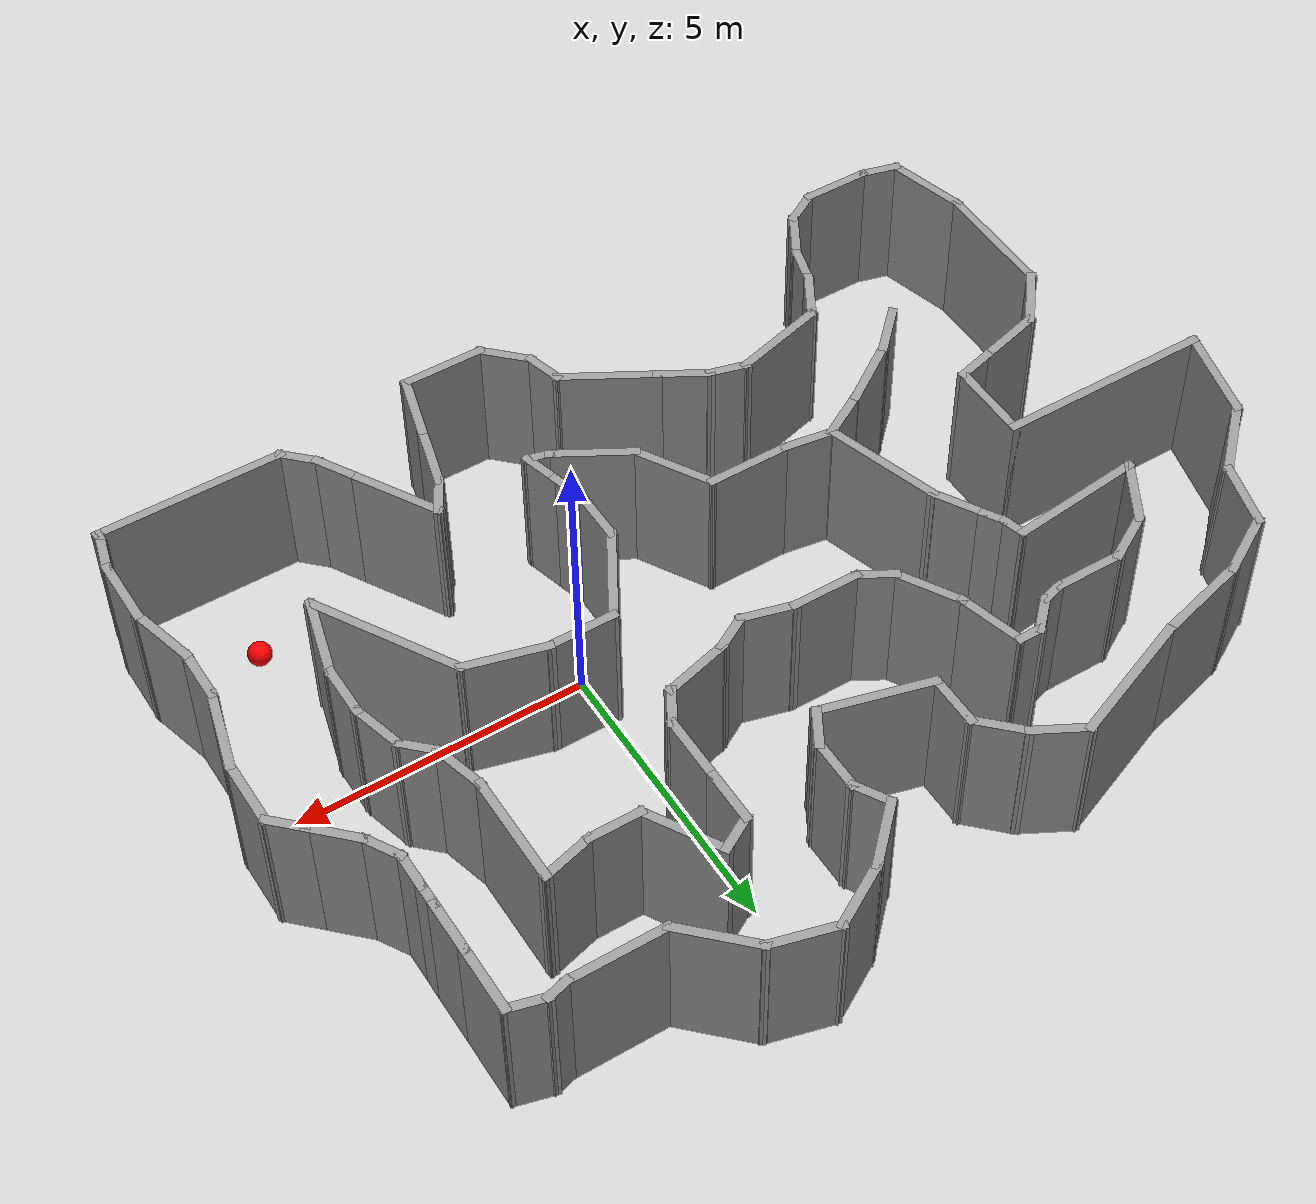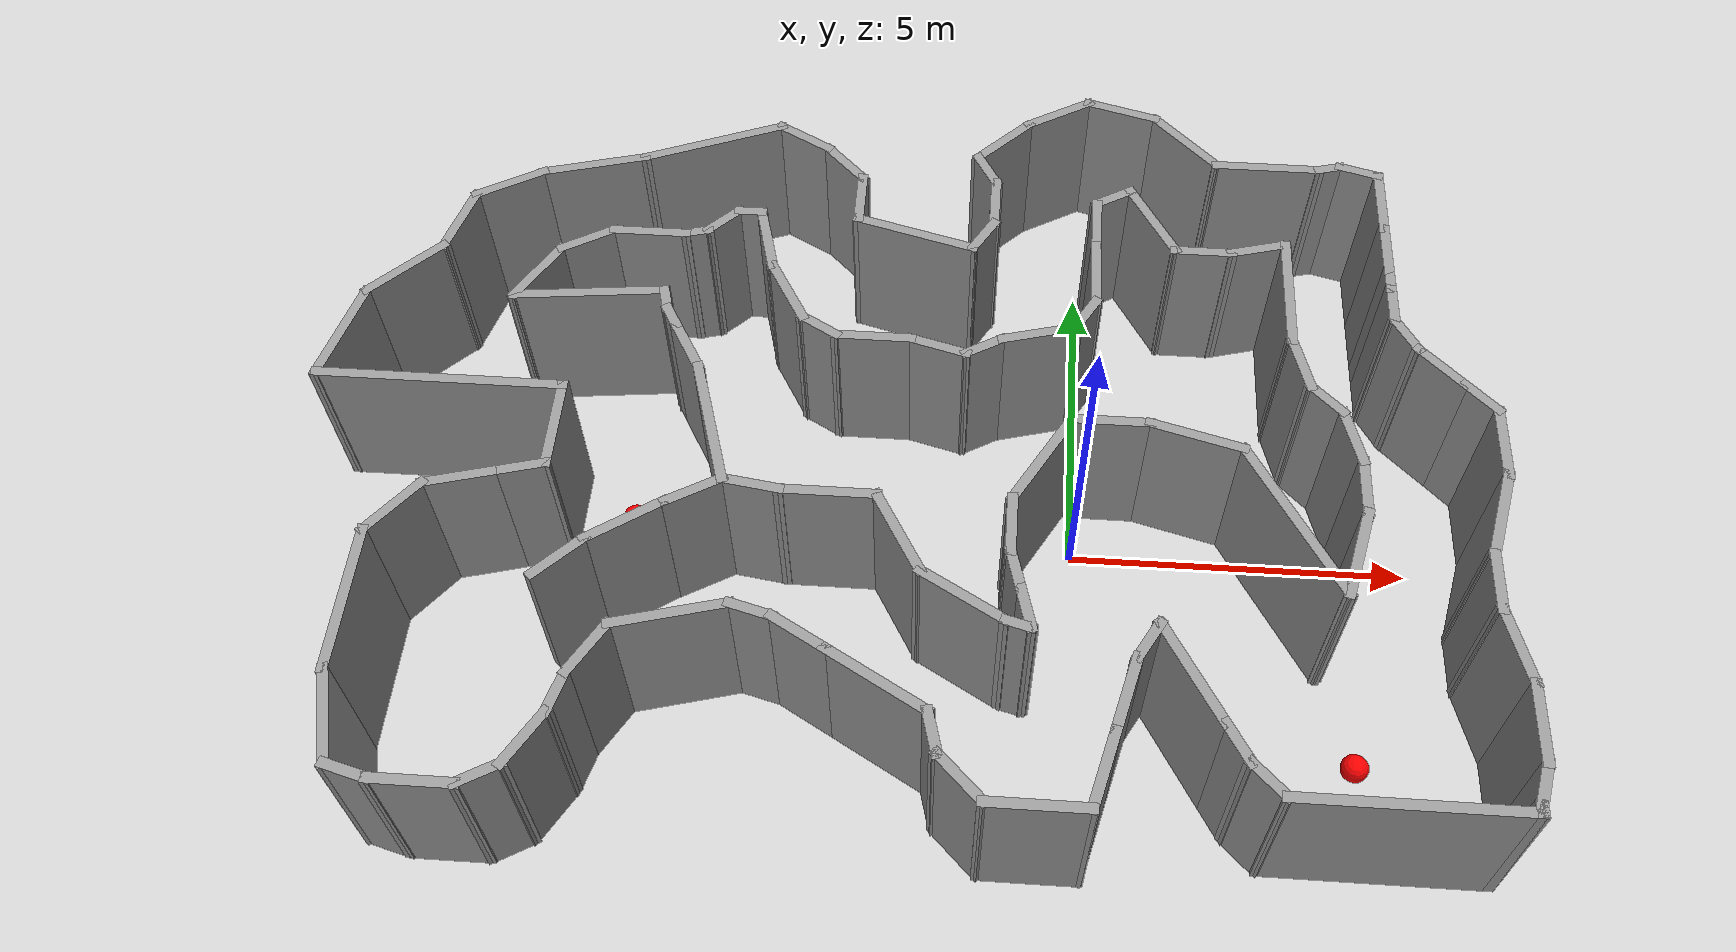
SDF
<?xml version='1.0'?>
<sdf version='1.7'>
  <model name='patrol_environment'>
    <static>true</static>
    <pose>-2.57827 0.945924 0 0 -0 0</pose>
    <link name='Wall_1'>
      <collision name='Wall_1_Collision'>
        <geometry>
          <box>
            <size>2.25 0.15 2.5</size>
          </box>
        </geometry>
        <pose>0 0 1.25 0 -0 0</pose>
      </collision>
      <visual name='Wall_1_Visual'>
        <pose>0 0 1.25 0 -0 0</pose>
        <geometry>
          <box>
            <size>2.25 0.15 2.5</size>
          </box>
        </geometry>
        <material>
          <script>
            <uri>file://media/materials/scripts/gazebo.material</uri>
            <name>Gazebo/Grey</name>
          </script>
          <ambient>1 1 1 1</ambient>
        </material>
        <meta>
          <layer>0</layer>
        </meta>
      </visual>
      <pose>-7.15359 -3.67328 0 0 -0 -1.5708</pose>
    </link>
    <link name='Wall_10'>
      <collision name='Wall_10_Collision'>
        <geometry>
          <box>
            <size>0.75 0.15 2.5</size>
          </box>
        </geometry>
        <pose>0 0 1.25 0 -0 0</pose>
      </collision>
      <visual name='Wall_10_Visual'>
        <pose>0 0 1.25 0 -0 0</pose>
        <geometry>
          <box>
            <size>0.75 0.15 2.5</size>
          </box>
        </geometry>
        <material>
          <script>
            <uri>file://media/materials/scripts/gazebo.material</uri>
            <name>Gazebo/Grey</name>
          </script>
          <ambient>1 1 1 1</ambient>
        </material>
        <meta>
          <layer>0</layer>
        </meta>
      </visual>
      <pose>-1.76447 -3.49431 0 0 -0 -0.261799</pose>
    </link>
    <link name='Wall_100'>
      <collision name='Wall_100_Collision'>
        <geometry>
          <box>
            <size>1.25 0.15 2.5</size>
          </box>
        </geometry>
        <pose>0 0 1.25 0 -0 0</pose>
      </collision>
      <visual name='Wall_100_Visual'>
        <pose>0 0 1.25 0 -0 0</pose>
        <geometry>
          <box>
            <size>1.25 0.15 2.5</size>
          </box>
        </geometry>
        <material>
          <script>
            <uri>file://media/materials/scripts/gazebo.material</uri>
            <name>Gazebo/Grey</name>
          </script>
          <ambient>1 1 1 1</ambient>
        </material>
        <meta>
          <layer>0</layer>
        </meta>
      </visual>
      <pose>2.97533 -0.124161 0 0 -0 3.14159</pose>
    </link>
    <link name='Wall_101'>
      <collision name='Wall_101_Collision'>
        <geometry>
          <box>
            <size>1.75 0.15 2.5</size>
          </box>
        </geometry>
        <pose>0 0 1.25 0 -0 0</pose>
      </collision>
      <visual name='Wall_101_Visual'>
        <pose>0 0 1.25 0 -0 0</pose>
        <geometry>
          <box>
            <size>1.75 0.15 2.5</size>
          </box>
        </geometry>
        <material>
          <script>
            <uri>file://media/materials/scripts/gazebo.material</uri>
            <name>Gazebo/Grey</name>
          </script>
          <ambient>1 1 1 1</ambient>
        </material>
        <meta>
          <layer>0</layer>
        </meta>
      </visual>
      <pose>2.02533 -0.816981 0 0 -0 -2.0944</pose>
    </link>
    <link name='Wall_102'>
      <collision name='Wall_102_Collision'>
        <geometry>
          <box>
            <size>1 0.15 2.5</size>
          </box>
        </geometry>
        <pose>0 0 1.25 0 -0 0</pose>
      </collision>
      <visual name='Wall_102_Visual'>
        <pose>0 0 1.25 0 -0 0</pose>
        <geometry>
          <box>
            <size>1 0.15 2.5</size>
          </box>
        </geometry>
        <material>
          <script>
            <uri>file://media/materials/scripts/gazebo.material</uri>
            <name>Gazebo/Grey</name>
          </script>
          <ambient>1 1 1 1</ambient>
        </material>
        <meta>
          <layer>0</layer>
        </meta>
      </visual>
      <pose>1.62533 -1.9348 0 0 -0 -1.5708</pose>
    </link>
    <link name='Wall_103'>
      <collision name='Wall_103_Collision'>
        <geometry>
          <box>
            <size>0.75 0.15 2.5</size>
          </box>
        </geometry>
        <pose>0 0 1.25 0 -0 0</pose>
      </collision>
      <visual name='Wall_103_Visual'>
        <pose>0 0 1.25 0 -0 0</pose>
        <geometry>
          <box>
            <size>0.75 0.15 2.5</size>
          </box>
        </geometry>
        <material>
          <script>
            <uri>file://media/materials/scripts/gazebo.material</uri>
            <name>Gazebo/Grey</name>
          </script>
          <ambient>1 1 1 1</ambient>
        </material>
        <meta>
          <layer>0</layer>
        </meta>
      </visual>
      <pose>1.70298 -2.64958 0 0 -0 -1.309</pose>
    </link>
    <link name='Wall_106'>
      <collision name='Wall_106_Collision'>
        <geometry>
          <box>
            <size>0.75 0.15 2.5</size>
          </box>
        </geometry>
        <pose>0 0 1.25 0 -0 0</pose>
      </collision>
      <visual name='Wall_106_Visual'>
        <pose>0 0 1.25 0 -0 0</pose>
        <geometry>
          <box>
            <size>0.75 0.15 2.5</size>
          </box>
        </geometry>
        <material>
          <script>
            <uri>file://media/materials/scripts/gazebo.material</uri>
            <name>Gazebo/Grey</name>
          </script>
          <ambient>1 1 1 1</ambient>
        </material>
        <meta>
          <layer>0</layer>
        </meta>
      </visual>
      <pose>1.85827 -3.22913 0 0 -0 -1.309</pose>
    </link>
    <link name='Wall_107'>
      <collision name='Wall_107_Collision'>
        <geometry>
          <box>
            <size>0.5 0.15 2.5</size>
          </box>
        </geometry>
        <pose>0 0 1.25 0 -0 0</pose>
      </collision>
      <visual name='Wall_107_Visual'>
        <pose>0 0 1.25 0 -0 0</pose>
        <geometry>
          <box>
            <size>0.5 0.15 2.5</size>
          </box>
        </geometry>
        <material>
          <script>
            <uri>file://media/materials/scripts/gazebo.material</uri>
            <name>Gazebo/Grey</name>
          </script>
          <ambient>1 1 1 1</ambient>
        </material>
        <meta>
          <layer>0</layer>
        </meta>
      </visual>
      <pose>1.76688 -3.47362 0 0 -0 2.87979</pose>
    </link>
    <link name='Wall_108'>
      <collision name='Wall_108_Collision'>
        <geometry>
          <box>
            <size>1.5 0.15 2.5</size>
          </box>
        </geometry>
        <pose>0 0 1.25 0 -0 0</pose>
      </collision>
      <visual name='Wall_108_Visual'>
        <pose>0 0 1.25 0 -0 0</pose>
        <geometry>
          <box>
            <size>1.5 0.15 2.5</size>
          </box>
        </geometry>
        <material>
          <script>
            <uri>file://media/materials/scripts/gazebo.material</uri>
            <name>Gazebo/Grey</name>
          </script>
          <ambient>1 1 1 1</ambient>
        </material>
        <meta>
          <layer>0</layer>
        </meta>
      </visual>
      <pose>1.01327 -3.09083 0 0 -0 2.61799</pose>
    </link>
    <link name='Wall_109'>
      <collision name='Wall_109_Collision'>
        <geometry>
          <box>
            <size>1.5 0.15 2.5</size>
          </box>
        </geometry>
        <pose>0 0 1.25 0 -0 0</pose>
      </collision>
      <visual name='Wall_109_Visual'>
        <pose>0 0 1.25 0 -0 0</pose>
        <geometry>
          <box>
            <size>1.5 0.15 2.5</size>
          </box>
        </geometry>
        <material>
          <script>
            <uri>file://media/materials/scripts/gazebo.material</uri>
            <name>Gazebo/Grey</name>
          </script>
          <ambient>1 1 1 1</ambient>
        </material>
        <meta>
          <layer>0</layer>
        </meta>
      </visual>
      <pose>0.091205 -2.16876 0 0 -0 2.0944</pose>
    </link>
    <link name='Wall_11'>
      <collision name='Wall_11_Collision'>
        <geometry>
          <box>
            <size>1 0.15 2.5</size>
          </box>
        </geometry>
        <pose>0 0 1.25 0 -0 0</pose>
      </collision>
      <visual name='Wall_11_Visual'>
        <pose>0 0 1.25 0 -0 0</pose>
        <geometry>
          <box>
            <size>1 0.15 2.5</size>
          </box>
        </geometry>
        <material>
          <script>
            <uri>file://media/materials/scripts/gazebo.material</uri>
            <name>Gazebo/Grey</name>
          </script>
          <ambient>1 1 1 1</ambient>
        </material>
        <meta>
          <layer>0</layer>
        </meta>
      </visual>
      <pose>-1.10663 -3.78446 0 0 -0 -0.523599</pose>
    </link>
    <link name='Wall_110'>
      <collision name='Wall_110_Collision'>
        <geometry>
          <box>
            <size>1.5 0.15 2.5</size>
          </box>
        </geometry>
        <pose>0 0 1.25 0 -0 0</pose>
      </collision>
      <visual name='Wall_110_Visual'>
        <pose>0 0 1.25 0 -0 0</pose>
        <geometry>
          <box>
            <size>1.5 0.15 2.5</size>
          </box>
        </geometry>
        <material>
          <script>
            <uri>file://media/materials/scripts/gazebo.material</uri>
            <name>Gazebo/Grey</name>
          </script>
          <ambient>1 1 1 1</ambient>
        </material>
        <meta>
          <layer>0</layer>
        </meta>
      </visual>
      <pose>-0.921295 -1.58419 0 0 -0 3.14159</pose>
    </link>
    <link name='Wall_111'>
      <collision name='Wall_111_Collision'>
        <geometry>
          <box>
            <size>0.96902 0.15 2.5</size>
          </box>
        </geometry>
        <pose>0 0 1.25 0 -0 0</pose>
      </collision>
      <visual name='Wall_111_Visual'>
        <pose>0 0 1.25 0 -0 0</pose>
        <geometry>
          <box>
            <size>0.96902 0.15 2.5</size>
          </box>
        </geometry>
        <material>
          <script>
            <uri>file://media/materials/scripts/gazebo.material</uri>
            <name>Gazebo/Grey</name>
          </script>
          <ambient>1 1 1 1</ambient>
        </material>
        <meta>
          <layer>0</layer>
        </meta>
      </visual>
      <pose>-2.00146 -1.52468 0 0 -0 2.99575</pose>
    </link>
    <link name='Wall_112'>
      <collision name='Wall_112_Collision'>
        <geometry>
          <box>
            <size>1 0.15 2.5</size>
          </box>
        </geometry>
        <pose>0 0 1.25 0 -0 0</pose>
      </collision>
      <visual name='Wall_112_Visual'>
        <pose>0 0 1.25 0 -0 0</pose>
        <geometry>
          <box>
            <size>1 0.15 2.5</size>
          </box>
        </geometry>
        <material>
          <script>
            <uri>file://media/materials/scripts/gazebo.material</uri>
            <name>Gazebo/Grey</name>
          </script>
          <ambient>1 1 1 1</ambient>
        </material>
        <meta>
          <layer>0</layer>
        </meta>
      </visual>
      <pose>-2.76146 -1.67767 0 0 -0 -2.61799</pose>
    </link>
    <link name='Wall_113'>
      <collision name='Wall_113_Collision'>
        <geometry>
          <box>
            <size>1.34677 0.15 2.5</size>
          </box>
        </geometry>
        <pose>0 0 1.25 0 -0 0</pose>
      </collision>
      <visual name='Wall_113_Visual'>
        <pose>0 0 1.25 0 -0 0</pose>
        <geometry>
          <box>
            <size>1.34677 0.15 2.5</size>
          </box>
        </geometry>
        <material>
          <script>
            <uri>file://media/materials/scripts/gazebo.material</uri>
            <name>Gazebo/Grey</name>
          </script>
          <ambient>1 1 1 1</ambient>
        </material>
        <meta>
          <layer>0</layer>
        </meta>
      </visual>
      <pose>-3.63889 -2.22468 0 0 -0 -2.54838</pose>
    </link>
    <link name='Wall_114'>
      <collision name='Wall_114_Collision'>
        <geometry>
          <box>
            <size>1 0.15 2.5</size>
          </box>
        </geometry>
        <pose>0 0 1.25 0 -0 0</pose>
      </collision>
      <visual name='Wall_114_Visual'>
        <pose>0 0 1.25 0 -0 0</pose>
        <geometry>
          <box>
            <size>1 0.15 2.5</size>
          </box>
        </geometry>
        <material>
          <script>
            <uri>file://media/materials/scripts/gazebo.material</uri>
            <name>Gazebo/Grey</name>
          </script>
          <ambient>1 1 1 1</ambient>
        </material>
        <meta>
          <layer>0</layer>
        </meta>
      </visual>
      <pose>-4.43557 -2.85971 0 0 -0 -2.35619</pose>
    </link>
    <link name='Wall_116'>
      <collision name='Wall_116_Collision'>
        <geometry>
          <box>
            <size>2.1465 0.15 2.5</size>
          </box>
        </geometry>
        <pose>0 0 1.25 0 -0 0</pose>
      </collision>
      <visual name='Wall_116_Visual'>
        <pose>0 0 1.25 0 -0 0</pose>
        <geometry>
          <box>
            <size>2.1465 0.15 2.5</size>
          </box>
        </geometry>
        <material>
          <script>
            <uri>file://media/materials/scripts/gazebo.material</uri>
            <name>Gazebo/Grey</name>
          </script>
          <ambient>1 1 1 1</ambient>
        </material>
        <meta>
          <layer>0</layer>
        </meta>
      </visual>
      <pose>-2.69822 -0.510457 0 0 -0 1.86723</pose>
    </link>
    <link name='Wall_117'>
      <collision name='Wall_117_Collision'>
        <geometry>
          <box>
            <size>1 0.15 2.5</size>
          </box>
        </geometry>
        <pose>0 0 1.25 0 -0 0</pose>
      </collision>
      <visual name='Wall_117_Visual'>
        <pose>0 0 1.25 0 -0 0</pose>
        <geometry>
          <box>
            <size>1 0.15 2.5</size>
          </box>
        </geometry>
        <material>
          <script>
            <uri>file://media/materials/scripts/gazebo.material</uri>
            <name>Gazebo/Grey</name>
          </script>
          <ambient>1 1 1 1</ambient>
        </material>
        <meta>
          <layer>0</layer>
        </meta>
      </visual>
      <pose>-3.20232 0.812314 0 0 -0 2.0944</pose>
    </link>
    <link name='Wall_118'>
      <collision name='Wall_118_Collision'>
        <geometry>
          <box>
            <size>0.5 0.15 2.5</size>
          </box>
        </geometry>
        <pose>0 0 1.25 0 -0 0</pose>
      </collision>
      <visual name='Wall_118_Visual'>
        <pose>0 0 1.25 0 -0 0</pose>
        <geometry>
          <box>
            <size>0.5 0.15 2.5</size>
          </box>
        </geometry>
        <material>
          <script>
            <uri>file://media/materials/scripts/gazebo.material</uri>
            <name>Gazebo/Grey</name>
          </script>
          <ambient>1 1 1 1</ambient>
        </material>
        <meta>
          <layer>0</layer>
        </meta>
      </visual>
      <pose>-3.50231 1.33193 0 0 -0 2.0944</pose>
    </link>
    <link name='Wall_119'>
      <collision name='Wall_119_Collision'>
        <geometry>
          <box>
            <size>0.5 0.15 2.5</size>
          </box>
        </geometry>
        <pose>0 0 1.25 0 -0 0</pose>
      </collision>
      <visual name='Wall_119_Visual'>
        <pose>0 0 1.25 0 -0 0</pose>
        <geometry>
          <box>
            <size>0.5 0.15 2.5</size>
          </box>
        </geometry>
        <material>
          <script>
            <uri>file://media/materials/scripts/gazebo.material</uri>
            <name>Gazebo/Grey</name>
          </script>
          <ambient>1 1 1 1</ambient>
        </material>
        <meta>
          <layer>0</layer>
        </meta>
      </visual>
      <pose>-3.63511 1.65252 0 0 -0 1.8326</pose>
    </link>
    <link name='Wall_12'>
      <collision name='Wall_12_Collision'>
        <geometry>
          <box>
            <size>1.75 0.15 2.5</size>
          </box>
        </geometry>
        <pose>0 0 1.25 0 -0 0</pose>
      </collision>
      <visual name='Wall_12_Visual'>
        <pose>0 0 1.25 0 -0 0</pose>
        <geometry>
          <box>
            <size>1.75 0.15 2.5</size>
          </box>
        </geometry>
        <material>
          <script>
            <uri>file://media/materials/scripts/gazebo.material</uri>
            <name>Gazebo/Grey</name>
          </script>
          <ambient>1 1 1 1</ambient>
        </material>
        <meta>
          <layer>0</layer>
        </meta>
      </visual>
      <pose>-0.045746 -4.39696 0 0 -0 -0.523599</pose>
    </link>
    <link name='Wall_120'>
      <collision name='Wall_120_Collision'>
        <geometry>
          <box>
            <size>2.3895 0.15 2.5</size>
          </box>
        </geometry>
        <pose>0 0 1.25 0 -0 0</pose>
      </collision>
      <visual name='Wall_120_Visual'>
        <pose>0 0 1.25 0 -0 0</pose>
        <geometry>
          <box>
            <size>2.3895 0.15 2.5</size>
          </box>
        </geometry>
        <material>
          <script>
            <uri>file://media/materials/scripts/gazebo.material</uri>
            <name>Gazebo/Grey</name>
          </script>
          <ambient>1 1 1 1</ambient>
        </material>
        <meta>
          <layer>0</layer>
        </meta>
      </visual>
      <pose>-4.79376 1.70207 0 0 -0 -3.03468</pose>
    </link>
    <link name='Wall_13'>
      <collision name='Wall_13_Collision'>
        <geometry>
          <box>
            <size>0.75 0.15 2.5</size>
          </box>
        </geometry>
        <pose>0 0 1.25 0 -0 0</pose>
      </collision>
      <visual name='Wall_13_Visual'>
        <pose>0 0 1.25 0 -0 0</pose>
        <geometry>
          <box>
            <size>0.75 0.15 2.5</size>
          </box>
        </geometry>
        <material>
          <script>
            <uri>file://media/materials/scripts/gazebo.material</uri>
            <name>Gazebo/Grey</name>
          </script>
          <ambient>1 1 1 1</ambient>
        </material>
        <meta>
          <layer>0</layer>
        </meta>
      </visual>
      <pose>0.72472 -5.08673 0 0 -0 -1.309</pose>
    </link>
    <link name='Wall_14'>
      <collision name='Wall_14_Collision'>
        <geometry>
          <box>
            <size>1 0.15 2.5</size>
          </box>
        </geometry>
        <pose>0 0 1.25 0 -0 0</pose>
      </collision>
      <visual name='Wall_14_Visual'>
        <pose>0 0 1.25 0 -0 0</pose>
        <geometry>
          <box>
            <size>1 0.15 2.5</size>
          </box>
        </geometry>
        <material>
          <script>
            <uri>file://media/materials/scripts/gazebo.material</uri>
            <name>Gazebo/Grey</name>
          </script>
          <ambient>1 1 1 1</ambient>
        </material>
        <meta>
          <layer>0</layer>
        </meta>
      </visual>
      <pose>1.10289 -5.67703 0 0 -0 -0.785398</pose>
    </link>
    <link name='Wall_15'>
      <collision name='Wall_15_Collision'>
        <geometry>
          <box>
            <size>1.5 0.15 2.5</size>
          </box>
        </geometry>
        <pose>0 0 1.25 0 -0 0</pose>
      </collision>
      <visual name='Wall_15_Visual'>
        <pose>0 0 1.25 0 -0 0</pose>
        <geometry>
          <box>
            <size>1.5 0.15 2.5</size>
          </box>
        </geometry>
        <material>
          <script>
            <uri>file://media/materials/scripts/gazebo.material</uri>
            <name>Gazebo/Grey</name>
          </script>
          <ambient>1 1 1 1</ambient>
        </material>
        <meta>
          <layer>0</layer>
        </meta>
      </visual>
      <pose>2.07841 -5.97755 0 0 -0 0</pose>
    </link>
    <link name='Wall_16'>
      <collision name='Wall_16_Collision'>
        <geometry>
          <box>
            <size>1.25 0.15 2.5</size>
          </box>
        </geometry>
        <pose>0 0 1.25 0 -0 0</pose>
      </collision>
      <visual name='Wall_16_Visual'>
        <pose>0 0 1.25 0 -0 0</pose>
        <geometry>
          <box>
            <size>1.25 0.15 2.5</size>
          </box>
        </geometry>
        <material>
          <script>
            <uri>file://media/materials/scripts/gazebo.material</uri>
            <name>Gazebo/Grey</name>
          </script>
          <ambient>1 1 1 1</ambient>
        </material>
        <meta>
          <layer>0</layer>
        </meta>
      </visual>
      <pose>2.89576 -5.44629 0 0 -0 1.309</pose>
    </link>
    <link name='Wall_17'>
      <collision name='Wall_17_Collision'>
        <geometry>
          <box>
            <size>1.25 0.15 2.5</size>
          </box>
        </geometry>
        <pose>0 0 1.25 0 -0 0</pose>
      </collision>
      <visual name='Wall_17_Visual'>
        <pose>0 0 1.25 0 -0 0</pose>
        <geometry>
          <box>
            <size>1.25 0.15 2.5</size>
          </box>
        </geometry>
        <material>
          <script>
            <uri>file://media/materials/scripts/gazebo.material</uri>
            <name>Gazebo/Grey</name>
          </script>
          <ambient>1 1 1 1</ambient>
        </material>
        <meta>
          <layer>0</layer>
        </meta>
      </visual>
      <pose>3.18046 -4.38377 0 0 -0 1.309</pose>
    </link>
    <link name='Wall_18'>
      <collision name='Wall_18_Collision'>
        <geometry>
          <box>
            <size>0.75 0.15 2.5</size>
          </box>
        </geometry>
        <pose>0 0 1.25 0 -0 0</pose>
      </collision>
      <visual name='Wall_18_Visual'>
        <pose>0 0 1.25 0 -0 0</pose>
        <geometry>
          <box>
            <size>0.75 0.15 2.5</size>
          </box>
        </geometry>
        <material>
          <script>
            <uri>file://media/materials/scripts/gazebo.material</uri>
            <name>Gazebo/Grey</name>
          </script>
          <ambient>1 1 1 1</ambient>
        </material>
        <meta>
          <layer>0</layer>
        </meta>
      </visual>
      <pose>3.47281 -3.59271 0 0 -0 1.0472</pose>
    </link>
    <link name='Wall_19'>
      <collision name='Wall_19_Collision'>
        <geometry>
          <box>
            <size>1.75 0.15 2.5</size>
          </box>
        </geometry>
        <pose>0 0 1.25 0 -0 0</pose>
      </collision>
      <visual name='Wall_19_Visual'>
        <pose>0 0 1.25 0 -0 0</pose>
        <geometry>
          <box>
            <size>1.75 0.15 2.5</size>
          </box>
        </geometry>
        <material>
          <script>
            <uri>file://media/materials/scripts/gazebo.material</uri>
            <name>Gazebo/Grey</name>
          </script>
          <ambient>1 1 1 1</ambient>
        </material>
        <meta>
          <layer>0</layer>
        </meta>
      </visual>
      <pose>4.02281 -4.02572 0 0 -0 -1.0472</pose>
    </link>
    <link name='Wall_2'>
      <collision name='Wall_2_Collision'>
        <geometry>
          <box>
            <size>1.5 0.15 2.5</size>
          </box>
        </geometry>
        <pose>0 0 1.25 0 -0 0</pose>
      </collision>
      <visual name='Wall_2_Visual'>
        <pose>0 0 1.25 0 -0 0</pose>
        <geometry>
          <box>
            <size>1.5 0.15 2.5</size>
          </box>
        </geometry>
        <material>
          <script>
            <uri>file://media/materials/scripts/gazebo.material</uri>
            <name>Gazebo/Grey</name>
          </script>
          <ambient>1 1 1 1</ambient>
        </material>
        <meta>
          <layer>0</layer>
        </meta>
      </visual>
      <pose>-6.97889 -5.37528 0 0 -0 -1.309</pose>
    </link>
    <link name='Wall_20'>
      <collision name='Wall_20_Collision'>
        <geometry>
          <box>
            <size>0.75 0.15 2.5</size>
          </box>
        </geometry>
        <pose>0 0 1.25 0 -0 0</pose>
      </collision>
      <visual name='Wall_20_Visual'>
        <pose>0 0 1.25 0 -0 0</pose>
        <geometry>
          <box>
            <size>0.75 0.15 2.5</size>
          </box>
        </geometry>
        <material>
          <script>
            <uri>file://media/materials/scripts/gazebo.material</uri>
            <name>Gazebo/Grey</name>
          </script>
          <ambient>1 1 1 1</ambient>
        </material>
        <meta>
          <layer>0</layer>
        </meta>
      </visual>
      <pose>4.57281 -4.97835 0 0 -0 -1.0472</pose>
    </link>
    <link name='Wall_21'>
      <collision name='Wall_21_Collision'>
        <geometry>
          <box>
            <size>0.75 0.15 2.5</size>
          </box>
        </geometry>
        <pose>0 0 1.25 0 -0 0</pose>
      </collision>
      <visual name='Wall_21_Visual'>
        <pose>0 0 1.25 0 -0 0</pose>
        <geometry>
          <box>
            <size>0.75 0.15 2.5</size>
          </box>
        </geometry>
        <material>
          <script>
            <uri>file://media/materials/scripts/gazebo.material</uri>
            <name>Gazebo/Grey</name>
          </script>
          <ambient>1 1 1 1</ambient>
        </material>
        <meta>
          <layer>0</layer>
        </meta>
      </visual>
      <pose>4.93494 -5.45029 0 0 -0 -0.785398</pose>
    </link>
    <link name='Wall_22'>
      <collision name='Wall_22_Collision'>
        <geometry>
          <box>
            <size>3.25 0.15 2.5</size>
          </box>
        </geometry>
        <pose>0 0 1.25 0 -0 0</pose>
      </collision>
      <visual name='Wall_22_Visual'>
        <pose>0 0 1.25 0 -0 0</pose>
        <geometry>
          <box>
            <size>3.25 0.15 2.5</size>
          </box>
        </geometry>
        <material>
          <script>
            <uri>file://media/materials/scripts/gazebo.material</uri>
            <name>Gazebo/Grey</name>
          </script>
          <ambient>1 1 1 1</ambient>
        </material>
        <meta>
          <layer>0</layer>
        </meta>
      </visual>
      <pose>6.69707 -5.66242 0 0 -0 0</pose>
    </link>
    <link name='Wall_23'>
      <collision name='Wall_23_Collision'>
        <geometry>
          <box>
            <size>0.25 0.15 2.5</size>
          </box>
        </geometry>
        <pose>0 0 1.25 0 -0 0</pose>
      </collision>
      <visual name='Wall_23_Visual'>
        <pose>0 0 1.25 0 -0 0</pose>
        <geometry>
          <box>
            <size>0.25 0.15 2.5</size>
          </box>
        </geometry>
        <material>
          <script>
            <uri>file://media/materials/scripts/gazebo.material</uri>
            <name>Gazebo/Grey</name>
          </script>
          <ambient>1 1 1 1</ambient>
        </material>
        <meta>
          <layer>0</layer>
        </meta>
      </visual>
      <pose>8.24707 -5.61242 0 0 -0 1.5708</pose>
    </link>
    <link name='Wall_24'>
      <collision name='Wall_24_Collision'>
        <geometry>
          <box>
            <size>0.75 0.15 2.5</size>
          </box>
        </geometry>
        <pose>0 0 1.25 0 -0 0</pose>
      </collision>
      <visual name='Wall_24_Visual'>
        <pose>0 0 1.25 0 -0 0</pose>
        <geometry>
          <box>
            <size>0.75 0.15 2.5</size>
          </box>
        </geometry>
        <material>
          <script>
            <uri>file://media/materials/scripts/gazebo.material</uri>
            <name>Gazebo/Grey</name>
          </script>
          <ambient>1 1 1 1</ambient>
        </material>
        <meta>
          <layer>0</layer>
        </meta>
      </visual>
      <pose>8.32472 -5.27264 0 0 -0 1.309</pose>
    </link>
    <link name='Wall_25'>
      <collision name='Wall_25_Collision'>
        <geometry>
          <box>
            <size>1.25 0.15 2.5</size>
          </box>
        </geometry>
        <pose>0 0 1.25 0 -0 0</pose>
      </collision>
      <visual name='Wall_25_Visual'>
        <pose>0 0 1.25 0 -0 0</pose>
        <geometry>
          <box>
            <size>1.25 0.15 2.5</size>
          </box>
        </geometry>
        <material>
          <script>
            <uri>file://media/materials/scripts/gazebo.material</uri>
            <name>Gazebo/Grey</name>
          </script>
          <ambient>1 1 1 1</ambient>
        </material>
        <meta>
          <layer>0</layer>
        </meta>
      </visual>
      <pose>8.40236 -4.43286 0 0 -0 1.5708</pose>
    </link>
    <link name='Wall_26'>
      <collision name='Wall_26_Collision'>
        <geometry>
          <box>
            <size>1.25 0.15 2.5</size>
          </box>
        </geometry>
        <pose>0 0 1.25 0 -0 0</pose>
      </collision>
      <visual name='Wall_26_Visual'>
        <pose>0 0 1.25 0 -0 0</pose>
        <geometry>
          <box>
            <size>1.25 0.15 2.5</size>
          </box>
        </geometry>
        <material>
          <script>
            <uri>file://media/materials/scripts/gazebo.material</uri>
            <name>Gazebo/Grey</name>
          </script>
          <ambient>1 1 1 1</ambient>
        </material>
        <meta>
          <layer>0</layer>
        </meta>
      </visual>
      <pose>8.26001 -3.35161 0 0 -0 1.8326</pose>
    </link>
    <link name='Wall_27'>
      <collision name='Wall_27_Collision'>
        <geometry>
          <box>
            <size>1 0.15 2.5</size>
          </box>
        </geometry>
        <pose>0 0 1.25 0 -0 0</pose>
      </collision>
      <visual name='Wall_27_Visual'>
        <pose>0 0 1.25 0 -0 0</pose>
        <geometry>
          <box>
            <size>1 0.15 2.5</size>
          </box>
        </geometry>
        <material>
          <script>
            <uri>file://media/materials/scripts/gazebo.material</uri>
            <name>Gazebo/Grey</name>
          </script>
          <ambient>1 1 1 1</ambient>
        </material>
        <meta>
          <layer>0</layer>
        </meta>
      </visual>
      <pose>8.11766 -2.39535 0 0 -0 1.5708</pose>
    </link>
    <link name='Wall_28'>
      <collision name='Wall_28_Collision'>
        <geometry>
          <box>
            <size>1.5 0.15 2.5</size>
          </box>
        </geometry>
        <pose>0 0 1.25 0 -0 0</pose>
      </collision>
      <visual name='Wall_28_Visual'>
        <pose>0 0 1.25 0 -0 0</pose>
        <geometry>
          <box>
            <size>1.5 0.15 2.5</size>
          </box>
        </geometry>
        <material>
          <script>
            <uri>file://media/materials/scripts/gazebo.material</uri>
            <name>Gazebo/Grey</name>
          </script>
          <ambient>1 1 1 1</ambient>
        </material>
        <meta>
          <layer>0</layer>
        </meta>
      </visual>
      <pose>8.29237 -1.31835 0 0 -0 1.309</pose>
    </link>
    <link name='Wall_29'>
      <collision name='Wall_29_Collision'>
        <geometry>
          <box>
            <size>1.25 0.15 2.5</size>
          </box>
        </geometry>
        <pose>0 0 1.25 0 -0 0</pose>
      </collision>
      <visual name='Wall_29_Visual'>
        <pose>0 0 1.25 0 -0 0</pose>
        <geometry>
          <box>
            <size>1.25 0.15 2.5</size>
          </box>
        </geometry>
        <material>
          <script>
            <uri>file://media/materials/scripts/gazebo.material</uri>
            <name>Gazebo/Grey</name>
          </script>
          <ambient>1 1 1 1</ambient>
        </material>
        <meta>
          <layer>0</layer>
        </meta>
      </visual>
      <pose>8.46707 -0.116346 0 0 -0 1.5708</pose>
    </link>
    <link name='Wall_3'>
      <collision name='Wall_3_Collision'>
        <geometry>
          <box>
            <size>0.75 0.15 2.5</size>
          </box>
        </geometry>
        <pose>0 0 1.25 0 -0 0</pose>
      </collision>
      <visual name='Wall_3_Visual'>
        <pose>0 0 1.25 0 -0 0</pose>
        <geometry>
          <box>
            <size>0.75 0.15 2.5</size>
          </box>
        </geometry>
        <material>
          <script>
            <uri>file://media/materials/scripts/gazebo.material</uri>
            <name>Gazebo/Grey</name>
          </script>
          <ambient>1 1 1 1</ambient>
        </material>
        <meta>
          <layer>0</layer>
        </meta>
      </visual>
      <pose>-6.51441 -6.10493 0 0 -0 -0.261799</pose>
    </link>
    <link name='Wall_30'>
      <collision name='Wall_30_Collision'>
        <geometry>
          <box>
            <size>0.75 0.15 2.5</size>
          </box>
        </geometry>
        <pose>0 0 1.25 0 -0 0</pose>
      </collision>
      <visual name='Wall_30_Visual'>
        <pose>0 0 1.25 0 -0 0</pose>
        <geometry>
          <box>
            <size>0.75 0.15 2.5</size>
          </box>
        </geometry>
        <material>
          <script>
            <uri>file://media/materials/scripts/gazebo.material</uri>
            <name>Gazebo/Grey</name>
          </script>
          <ambient>1 1 1 1</ambient>
        </material>
        <meta>
          <layer>0</layer>
        </meta>
      </visual>
      <pose>8.25494 0.645786 0 0 -0 2.35619</pose>
    </link>
    <link name='Wall_31'>
      <collision name='Wall_31_Collision'>
        <geometry>
          <box>
            <size>1 0.15 2.5</size>
          </box>
        </geometry>
        <pose>0 0 1.25 0 -0 0</pose>
      </collision>
      <visual name='Wall_31_Visual'>
        <pose>0 0 1.25 0 -0 0</pose>
        <geometry>
          <box>
            <size>1 0.15 2.5</size>
          </box>
        </geometry>
        <material>
          <script>
            <uri>file://media/materials/scripts/gazebo.material</uri>
            <name>Gazebo/Grey</name>
          </script>
          <ambient>1 1 1 1</ambient>
        </material>
        <meta>
          <layer>0</layer>
        </meta>
      </visual>
      <pose>7.74228 1.15844 0 0 -0 2.35619</pose>
    </link>
    <link name='Wall_32'>
      <collision name='Wall_32_Collision'>
        <geometry>
          <box>
            <size>0.75 0.15 2.5</size>
          </box>
        </geometry>
        <pose>0 0 1.25 0 -0 0</pose>
      </collision>
      <visual name='Wall_32_Visual'>
        <pose>0 0 1.25 0 -0 0</pose>
        <geometry>
          <box>
            <size>0.75 0.15 2.5</size>
          </box>
        </geometry>
        <material>
          <script>
            <uri>file://media/materials/scripts/gazebo.material</uri>
            <name>Gazebo/Grey</name>
          </script>
          <ambient>1 1 1 1</ambient>
        </material>
        <meta>
          <layer>0</layer>
        </meta>
      </visual>
      <pose>7.29176 1.71877 0 0 -0 2.0944</pose>
    </link>
    <link name='Wall_33'>
      <collision name='Wall_33_Collision'>
        <geometry>
          <box>
            <size>0.75 0.15 2.5</size>
          </box>
        </geometry>
        <pose>0 0 1.25 0 -0 0</pose>
      </collision>
      <visual name='Wall_33_Visual'>
        <pose>0 0 1.25 0 -0 0</pose>
        <geometry>
          <box>
            <size>0.75 0.15 2.5</size>
          </box>
        </geometry>
        <material>
          <script>
            <uri>file://media/materials/scripts/gazebo.material</uri>
            <name>Gazebo/Grey</name>
          </script>
          <ambient>1 1 1 1</ambient>
        </material>
        <meta>
          <layer>0</layer>
        </meta>
      </visual>
      <pose>7.14176 2.27857 0 0 -0 1.5708</pose>
    </link>
    <link name='Wall_34'>
      <collision name='Wall_34_Collision'>
        <geometry>
          <box>
            <size>0.5 0.15 2.5</size>
          </box>
        </geometry>
        <pose>0 0 1.25 0 -0 0</pose>
      </collision>
      <visual name='Wall_34_Visual'>
        <pose>0 0 1.25 0 -0 0</pose>
        <geometry>
          <box>
            <size>0.5 0.15 2.5</size>
          </box>
        </geometry>
        <material>
          <script>
            <uri>file://media/materials/scripts/gazebo.material</uri>
            <name>Gazebo/Grey</name>
          </script>
          <ambient>1 1 1 1</ambient>
        </material>
        <meta>
          <layer>0</layer>
        </meta>
      </visual>
      <pose>7.14176 2.75357 0 0 -0 1.5708</pose>
    </link>
    <link name='Wall_35'>
      <collision name='Wall_35_Collision'>
        <geometry>
          <box>
            <size>1 0.15 2.5</size>
          </box>
        </geometry>
        <pose>0 0 1.25 0 -0 0</pose>
      </collision>
      <visual name='Wall_35_Visual'>
        <pose>0 0 1.25 0 -0 0</pose>
        <geometry>
          <box>
            <size>1 0.15 2.5</size>
          </box>
        </geometry>
        <material>
          <script>
            <uri>file://media/materials/scripts/gazebo.material</uri>
            <name>Gazebo/Grey</name>
          </script>
          <ambient>1 1 1 1</ambient>
        </material>
        <meta>
          <layer>0</layer>
        </meta>
      </visual>
      <pose>7.14176 3.35357 0 0 -0 1.5708</pose>
    </link>
    <link name='Wall_36'>
      <collision name='Wall_36_Collision'>
        <geometry>
          <box>
            <size>1.25 0.15 2.5</size>
          </box>
        </geometry>
        <pose>0 0 1.25 0 -0 0</pose>
      </collision>
      <visual name='Wall_36_Visual'>
        <pose>0 0 1.25 0 -0 0</pose>
        <geometry>
          <box>
            <size>1.25 0.15 2.5</size>
          </box>
        </geometry>
        <material>
          <script>
            <uri>file://media/materials/scripts/gazebo.material</uri>
            <name>Gazebo/Grey</name>
          </script>
          <ambient>1 1 1 1</ambient>
        </material>
        <meta>
          <layer>0</layer>
        </meta>
      </visual>
      <pose>7.14176 4.32857 0 0 -0 1.5708</pose>
    </link>
    <link name='Wall_37'>
      <collision name='Wall_37_Collision'>
        <geometry>
          <box>
            <size>0.75 0.15 2.5</size>
          </box>
        </geometry>
        <pose>0 0 1.25 0 -0 0</pose>
      </collision>
      <visual name='Wall_37_Visual'>
        <pose>0 0 1.25 0 -0 0</pose>
        <geometry>
          <box>
            <size>0.75 0.15 2.5</size>
          </box>
        </geometry>
        <material>
          <script>
            <uri>file://media/materials/scripts/gazebo.material</uri>
            <name>Gazebo/Grey</name>
          </script>
          <ambient>1 1 1 1</ambient>
        </material>
        <meta>
          <layer>0</layer>
        </meta>
      </visual>
      <pose>6.85199 4.95622 0 0 -0 2.87979</pose>
    </link>
    <link name='Wall_38'>
      <collision name='Wall_38_Collision'>
        <geometry>
          <box>
            <size>0.5 0.15 2.5</size>
          </box>
        </geometry>
        <pose>0 0 1.25 0 -0 0</pose>
      </collision>
      <visual name='Wall_38_Visual'>
        <pose>0 0 1.25 0 -0 0</pose>
        <geometry>
          <box>
            <size>0.5 0.15 2.5</size>
          </box>
        </geometry>
        <material>
          <script>
            <uri>file://media/materials/scripts/gazebo.material</uri>
            <name>Gazebo/Grey</name>
          </script>
          <ambient>1 1 1 1</ambient>
        </material>
        <meta>
          <layer>0</layer>
        </meta>
      </visual>
      <pose>6.39317 4.98857 0 0 -0 -2.87979</pose>
    </link>
    <link name='Wall_4'>
      <collision name='Wall_4_Collision'>
        <geometry>
          <box>
            <size>1.25 0.15 2.5</size>
          </box>
        </geometry>
        <pose>0 0 1.25 0 -0 0</pose>
      </collision>
      <visual name='Wall_4_Visual'>
        <pose>0 0 1.25 0 -0 0</pose>
        <geometry>
          <box>
            <size>1.25 0.15 2.5</size>
          </box>
        </geometry>
        <material>
          <script>
            <uri>file://media/materials/scripts/gazebo.material</uri>
            <name>Gazebo/Grey</name>
          </script>
          <ambient>1 1 1 1</ambient>
        </material>
        <meta>
          <layer>0</layer>
        </meta>
      </visual>
      <pose>-5.67463 -6.18257 0 0 -0 0</pose>
    </link>
    <link name='Wall_40'>
      <collision name='Wall_40_Collision'>
        <geometry>
          <box>
            <size>1.75 0.15 2.5</size>
          </box>
        </geometry>
        <pose>0 0 1.25 0 -0 0</pose>
      </collision>
      <visual name='Wall_40_Visual'>
        <pose>0 0 1.25 0 -0 0</pose>
        <geometry>
          <box>
            <size>1.75 0.15 2.5</size>
          </box>
        </geometry>
        <material>
          <script>
            <uri>file://media/materials/scripts/gazebo.material</uri>
            <name>Gazebo/Grey</name>
          </script>
          <ambient>1 1 1 1</ambient>
        </material>
        <meta>
          <layer>0</layer>
        </meta>
      </visual>
      <pose>5.42413 4.94328 0 0 -0 3.14159</pose>
    </link>
    <link name='Wall_41'>
      <collision name='Wall_41_Collision'>
        <geometry>
          <box>
            <size>1.5 0.15 2.5</size>
          </box>
        </geometry>
        <pose>0 0 1.25 0 -0 0</pose>
      </collision>
      <visual name='Wall_41_Visual'>
        <pose>0 0 1.25 0 -0 0</pose>
        <geometry>
          <box>
            <size>1.5 0.15 2.5</size>
          </box>
        </geometry>
        <material>
          <script>
            <uri>file://media/materials/scripts/gazebo.material</uri>
            <name>Gazebo/Grey</name>
          </script>
          <ambient>1 1 1 1</ambient>
        </material>
        <meta>
          <layer>0</layer>
        </meta>
      </visual>
      <pose>4.14684 5.42058 0 0 -0 2.35619</pose>
    </link>
    <link name='Wall_42'>
      <collision name='Wall_42_Collision'>
        <geometry>
          <box>
            <size>1.25 0.15 2.5</size>
          </box>
        </geometry>
        <pose>0 0 1.25 0 -0 0</pose>
      </collision>
      <visual name='Wall_42_Visual'>
        <pose>0 0 1.25 0 -0 0</pose>
        <geometry>
          <box>
            <size>1.25 0.15 2.5</size>
          </box>
        </geometry>
        <material>
          <script>
            <uri>file://media/materials/scripts/gazebo.material</uri>
            <name>Gazebo/Grey</name>
          </script>
          <ambient>1 1 1 1</ambient>
        </material>
        <meta>
          <layer>0</layer>
        </meta>
      </visual>
      <pose>3.13828 6.04022 0 0 -0 2.87979</pose>
    </link>
    <link name='Wall_43'>
      <collision name='Wall_43_Collision'>
        <geometry>
          <box>
            <size>1.25 0.15 2.5</size>
          </box>
        </geometry>
        <pose>0 0 1.25 0 -0 0</pose>
      </collision>
      <visual name='Wall_43_Visual'>
        <pose>0 0 1.25 0 -0 0</pose>
        <geometry>
          <box>
            <size>1.25 0.15 2.5</size>
          </box>
        </geometry>
        <material>
          <script>
            <uri>file://media/materials/scripts/gazebo.material</uri>
            <name>Gazebo/Grey</name>
          </script>
          <ambient>1 1 1 1</ambient>
        </material>
        <meta>
          <layer>0</layer>
        </meta>
      </visual>
      <pose>2.13071 5.90757 0 0 -0 -2.61799</pose>
    </link>
    <link name='Wall_44'>
      <collision name='Wall_44_Collision'>
        <geometry>
          <box>
            <size>1.25 0.15 2.5</size>
          </box>
        </geometry>
        <pose>0 0 1.25 0 -0 0</pose>
      </collision>
      <visual name='Wall_44_Visual'>
        <pose>0 0 1.25 0 -0 0</pose>
        <geometry>
          <box>
            <size>1.25 0.15 2.5</size>
          </box>
        </geometry>
        <material>
          <script>
            <uri>file://media/materials/scripts/gazebo.material</uri>
            <name>Gazebo/Grey</name>
          </script>
          <ambient>1 1 1 1</ambient>
        </material>
        <meta>
          <layer>0</layer>
        </meta>
      </visual>
      <pose>1.26548 5.24367 0 0 -0 -2.35619</pose>
    </link>
    <link name='Wall_45'>
      <collision name='Wall_45_Collision'>
        <geometry>
          <box>
            <size>0.75 0.15 2.5</size>
          </box>
        </geometry>
        <pose>0 0 1.25 0 -0 0</pose>
      </collision>
      <visual name='Wall_45_Visual'>
        <pose>0 0 1.25 0 -0 0</pose>
        <geometry>
          <box>
            <size>0.75 0.15 2.5</size>
          </box>
        </geometry>
        <material>
          <script>
            <uri>file://media/materials/scripts/gazebo.material</uri>
            <name>Gazebo/Grey</name>
          </script>
          <ambient>1 1 1 1</ambient>
        </material>
        <meta>
          <layer>0</layer>
        </meta>
      </visual>
      <pose>1.02658 4.59495 0 0 -0 -1.0472</pose>
    </link>
    <link name='Wall_46'>
      <collision name='Wall_46_Collision'>
        <geometry>
          <box>
            <size>1 0.15 2.5</size>
          </box>
        </geometry>
        <pose>0 0 1.25 0 -0 0</pose>
      </collision>
      <visual name='Wall_46_Visual'>
        <pose>0 0 1.25 0 -0 0</pose>
        <geometry>
          <box>
            <size>1 0.15 2.5</size>
          </box>
        </geometry>
        <material>
          <script>
            <uri>file://media/materials/scripts/gazebo.material</uri>
            <name>Gazebo/Grey</name>
          </script>
          <ambient>1 1 1 1</ambient>
        </material>
        <meta>
          <layer>0</layer>
        </meta>
      </visual>
      <pose>1.17658 3.91014 0 0 -0 -1.5708</pose>
    </link>
    <link name='Wall_47'>
      <collision name='Wall_47_Collision'>
        <geometry>
          <box>
            <size>0.75 0.15 2.5</size>
          </box>
        </geometry>
        <pose>0 0 1.25 0 -0 0</pose>
      </collision>
      <visual name='Wall_47_Visual'>
        <pose>0 0 1.25 0 -0 0</pose>
        <geometry>
          <box>
            <size>0.75 0.15 2.5</size>
          </box>
        </geometry>
        <material>
          <script>
            <uri>file://media/materials/scripts/gazebo.material</uri>
            <name>Gazebo/Grey</name>
          </script>
          <ambient>1 1 1 1</ambient>
        </material>
        <meta>
          <layer>0</layer>
        </meta>
      </visual>
      <pose>1.02658 3.22533 0 0 -0 -2.0944</pose>
    </link>
    <link name='Wall_48'>
      <collision name='Wall_48_Collision'>
        <geometry>
          <box>
            <size>2 0.15 2.5</size>
          </box>
        </geometry>
        <pose>0 0 1.25 0 -0 0</pose>
      </collision>
      <visual name='Wall_48_Visual'>
        <pose>0 0 1.25 0 -0 0</pose>
        <geometry>
          <box>
            <size>2 0.15 2.5</size>
          </box>
        </geometry>
        <material>
          <script>
            <uri>file://media/materials/scripts/gazebo.material</uri>
            <name>Gazebo/Grey</name>
          </script>
          <ambient>1 1 1 1</ambient>
        </material>
        <meta>
          <layer>0</layer>
        </meta>
      </visual>
      <pose>-0.016905 3.20493 0 0 -0 2.87979</pose>
    </link>
    <link name='Wall_49'>
      <collision name='Wall_49_Collision'>
        <geometry>
          <box>
            <size>1 0.15 2.5</size>
          </box>
        </geometry>
        <pose>0 0 1.25 0 -0 0</pose>
      </collision>
      <visual name='Wall_49_Visual'>
        <pose>0 0 1.25 0 -0 0</pose>
        <geometry>
          <box>
            <size>1 0.15 2.5</size>
          </box>
        </geometry>
        <material>
          <script>
            <uri>file://media/materials/scripts/gazebo.material</uri>
            <name>Gazebo/Grey</name>
          </script>
          <ambient>1 1 1 1</ambient>
        </material>
        <meta>
          <layer>0</layer>
        </meta>
      </visual>
      <pose>-0.910387 3.86934 0 0 -0 1.5708</pose>
    </link>
    <link name='Wall_5'>
      <collision name='Wall_5_Collision'>
        <geometry>
          <box>
            <size>0.75 0.15 2.5</size>
          </box>
        </geometry>
        <pose>0 0 1.25 0 -0 0</pose>
      </collision>
      <visual name='Wall_5_Visual'>
        <pose>0 0 1.25 0 -0 0</pose>
        <geometry>
          <box>
            <size>0.75 0.15 2.5</size>
          </box>
        </geometry>
        <material>
          <script>
            <uri>file://media/materials/scripts/gazebo.material</uri>
            <name>Gazebo/Grey</name>
          </script>
          <ambient>1 1 1 1</ambient>
        </material>
        <meta>
          <layer>0</layer>
        </meta>
      </visual>
      <pose>-4.86482 -6.03257 0 0 -0 0.523599</pose>
    </link>
    <link name='Wall_50'>
      <collision name='Wall_50_Collision'>
        <geometry>
          <box>
            <size>1 0.15 2.5</size>
          </box>
        </geometry>
        <pose>0 0 1.25 0 -0 0</pose>
      </collision>
      <visual name='Wall_50_Visual'>
        <pose>0 0 1.25 0 -0 0</pose>
        <geometry>
          <box>
            <size>1 0.15 2.5</size>
          </box>
        </geometry>
        <material>
          <script>
            <uri>file://media/materials/scripts/gazebo.material</uri>
            <name>Gazebo/Grey</name>
          </script>
          <ambient>1 1 1 1</ambient>
        </material>
        <meta>
          <layer>0</layer>
        </meta>
      </visual>
      <pose>-1.21091 4.59486 0 0 -0 2.35619</pose>
    </link>
    <link name='Wall_51'>
      <collision name='Wall_51_Collision'>
        <geometry>
          <box>
            <size>1.04036 0.15 2.5</size>
          </box>
        </geometry>
        <pose>0 0 1.25 0 -0 0</pose>
      </collision>
      <visual name='Wall_51_Visual'>
        <pose>0 0 1.25 0 -0 0</pose>
        <geometry>
          <box>
            <size>1.04036 0.15 2.5</size>
          </box>
        </geometry>
        <material>
          <script>
            <uri>file://media/materials/scripts/gazebo.material</uri>
            <name>Gazebo/Grey</name>
          </script>
          <ambient>1 1 1 1</ambient>
        </material>
        <meta>
          <layer>0</layer>
        </meta>
      </visual>
      <pose>-1.90262 5.10788 0 0 -0 2.64398</pose>
    </link>
    <link name='Wall_54'>
      <collision name='Wall_54_Collision'>
        <geometry>
          <box>
            <size>1.75 0.15 2.5</size>
          </box>
        </geometry>
        <pose>0 0 1.25 0 -0 0</pose>
      </collision>
      <visual name='Wall_54_Visual'>
        <pose>0 0 1.25 0 -0 0</pose>
        <geometry>
          <box>
            <size>1.75 0.15 2.5</size>
          </box>
        </geometry>
        <material>
          <script>
            <uri>file://media/materials/scripts/gazebo.material</uri>
            <name>Gazebo/Grey</name>
          </script>
          <ambient>1 1 1 1</ambient>
        </material>
        <meta>
          <layer>0</layer>
        </meta>
      </visual>
      <pose>-5.15029 4.29229 0 0 -0 -2.87979</pose>
    </link>
    <link name='Wall_55'>
      <collision name='Wall_55_Collision'>
        <geometry>
          <box>
            <size>1.25 0.15 2.5</size>
          </box>
        </geometry>
        <pose>0 0 1.25 0 -0 0</pose>
      </collision>
      <visual name='Wall_55_Visual'>
        <pose>0 0 1.25 0 -0 0</pose>
        <geometry>
          <box>
            <size>1.25 0.15 2.5</size>
          </box>
        </geometry>
        <material>
          <script>
            <uri>file://media/materials/scripts/gazebo.material</uri>
            <name>Gazebo/Grey</name>
          </script>
          <ambient>1 1 1 1</ambient>
        </material>
        <meta>
          <layer>0</layer>
        </meta>
      </visual>
      <pose>-6.39935 3.81023 0 0 -0 -2.61799</pose>
    </link>
    <link name='Wall_56'>
      <collision name='Wall_56_Collision'>
        <geometry>
          <box>
            <size>1.25 0.15 2.5</size>
          </box>
        </geometry>
        <pose>0 0 1.25 0 -0 0</pose>
      </collision>
      <visual name='Wall_56_Visual'>
        <pose>0 0 1.25 0 -0 0</pose>
        <geometry>
          <box>
            <size>1.25 0.15 2.5</size>
          </box>
        </geometry>
        <material>
          <script>
            <uri>file://media/materials/scripts/gazebo.material</uri>
            <name>Gazebo/Grey</name>
          </script>
          <ambient>1 1 1 1</ambient>
        </material>
        <meta>
          <layer>0</layer>
        </meta>
      </visual>
      <pose>-7.01801 3.00398 0 0 -0 -1.8326</pose>
    </link>
    <link name='Wall_57'>
      <collision name='Wall_57_Collision'>
        <geometry>
          <box>
            <size>1.5 0.15 2.5</size>
          </box>
        </geometry>
        <pose>0 0 1.25 0 -0 0</pose>
      </collision>
      <visual name='Wall_57_Visual'>
        <pose>0 0 1.25 0 -0 0</pose>
        <geometry>
          <box>
            <size>1.5 0.15 2.5</size>
          </box>
        </geometry>
        <material>
          <script>
            <uri>file://media/materials/scripts/gazebo.material</uri>
            <name>Gazebo/Grey</name>
          </script>
          <ambient>1 1 1 1</ambient>
        </material>
        <meta>
          <layer>0</layer>
        </meta>
      </visual>
      <pose>-7.63766 1.99542 0 0 -0 -2.35619</pose>
    </link>
    <link name='Wall_58'>
      <collision name='Wall_58_Collision'>
        <geometry>
          <box>
            <size>1.73866 0.15 2.5</size>
          </box>
        </geometry>
        <pose>0 0 1.25 0 -0 0</pose>
      </collision>
      <visual name='Wall_58_Visual'>
        <pose>0 0 1.25 0 -0 0</pose>
        <geometry>
          <box>
            <size>1.73866 0.15 2.5</size>
          </box>
        </geometry>
        <material>
          <script>
            <uri>file://media/materials/scripts/gazebo.material</uri>
            <name>Gazebo/Grey</name>
          </script>
          <ambient>1 1 1 1</ambient>
        </material>
        <meta>
          <layer>0</layer>
        </meta>
      </visual>
      <pose>-8.29888 0.745381 0 0 -0 -1.80446</pose>
    </link>
    <link name='Wall_6'>
      <collision name='Wall_6_Collision'>
        <geometry>
          <box>
            <size>1 0.15 2.5</size>
          </box>
        </geometry>
        <pose>0 0 1.25 0 -0 0</pose>
      </collision>
      <visual name='Wall_6_Visual'>
        <pose>0 0 1.25 0 -0 0</pose>
        <geometry>
          <box>
            <size>1 0.15 2.5</size>
          </box>
        </geometry>
        <material>
          <script>
            <uri>file://media/materials/scripts/gazebo.material</uri>
            <name>Gazebo/Grey</name>
          </script>
          <ambient>1 1 1 1</ambient>
        </material>
        <meta>
          <layer>0</layer>
        </meta>
      </visual>
      <pose>-4.39252 -5.51451 0 0 -0 1.0472</pose>
    </link>
    <link name='Wall_63'>
      <collision name='Wall_63_Collision'>
        <geometry>
          <box>
            <size>3.75 0.15 2.5</size>
          </box>
        </geometry>
        <pose>0 0 1.25 0 -0 0</pose>
      </collision>
      <visual name='Wall_63_Visual'>
        <pose>0 0 1.25 0 -0 0</pose>
        <geometry>
          <box>
            <size>3.75 0.15 2.5</size>
          </box>
        </geometry>
        <material>
          <script>
            <uri>file://media/materials/scripts/gazebo.material</uri>
            <name>Gazebo/Grey</name>
          </script>
          <ambient>1 1 1 1</ambient>
        </material>
        <meta>
          <layer>0</layer>
        </meta>
      </visual>
      <pose>-6.68281 -0.02736 0 0 -0 0</pose>
    </link>
    <link name='Wall_64'>
      <collision name='Wall_64_Collision'>
        <geometry>
          <box>
            <size>1.5 0.15 2.5</size>
          </box>
        </geometry>
        <pose>0 0 1.25 0 -0 0</pose>
      </collision>
      <visual name='Wall_64_Visual'>
        <pose>0 0 1.25 0 -0 0</pose>
        <geometry>
          <box>
            <size>1.5 0.15 2.5</size>
          </box>
        </geometry>
        <material>
          <script>
            <uri>file://media/materials/scripts/gazebo.material</uri>
            <name>Gazebo/Grey</name>
          </script>
          <ambient>1 1 1 1</ambient>
        </material>
        <meta>
          <layer>0</layer>
        </meta>
      </visual>
      <pose>-4.88281 -0.70236 0 0 -0 -1.5708</pose>
    </link>
    <link name='Wall_65'>
      <collision name='Wall_65_Collision'>
        <geometry>
          <box>
            <size>0.75 0.15 2.5</size>
          </box>
        </geometry>
        <pose>0 0 1.25 0 -0 0</pose>
      </collision>
      <visual name='Wall_65_Visual'>
        <pose>0 0 1.25 0 -0 0</pose>
        <geometry>
          <box>
            <size>0.75 0.15 2.5</size>
          </box>
        </geometry>
        <material>
          <script>
            <uri>file://media/materials/scripts/gazebo.material</uri>
            <name>Gazebo/Grey</name>
          </script>
          <ambient>1 1 1 1</ambient>
        </material>
        <meta>
          <layer>0</layer>
        </meta>
      </visual>
      <pose>-5.17258 -1.45501 0 0 -0 -2.87979</pose>
    </link>
    <link name='Wall_66'>
      <collision name='Wall_66_Collision'>
        <geometry>
          <box>
            <size>1.25 0.15 2.5</size>
          </box>
        </geometry>
        <pose>0 0 1.25 0 -0 0</pose>
      </collision>
      <visual name='Wall_66_Visual'>
        <pose>0 0 1.25 0 -0 0</pose>
        <geometry>
          <box>
            <size>1.25 0.15 2.5</size>
          </box>
        </geometry>
        <material>
          <script>
            <uri>file://media/materials/scripts/gazebo.material</uri>
            <name>Gazebo/Grey</name>
          </script>
          <ambient>1 1 1 1</ambient>
        </material>
        <meta>
          <layer>0</layer>
        </meta>
      </visual>
      <pose>-5.99362 -1.675 0 0 -0 -2.87979</pose>
    </link>
    <link name='Wall_67'>
      <collision name='Wall_67_Collision'>
        <geometry>
          <box>
            <size>1.17216 0.15 2.5</size>
          </box>
        </geometry>
        <pose>0 0 1.25 0 -0 0</pose>
      </collision>
      <visual name='Wall_67_Visual'>
        <pose>0 0 1.25 0 -0 0</pose>
        <geometry>
          <box>
            <size>1.17216 0.15 2.5</size>
          </box>
        </geometry>
        <material>
          <script>
            <uri>file://media/materials/scripts/gazebo.material</uri>
            <name>Gazebo/Grey</name>
          </script>
          <ambient>1 1 1 1</ambient>
        </material>
        <meta>
          <layer>0</layer>
        </meta>
      </visual>
      <pose>-6.83924 -2.22032 0 0 -0 -2.23329</pose>
    </link>
    <link name='Wall_69'>
      <collision name='Wall_69_Collision'>
        <geometry>
          <box>
            <size>2.38966 0.15 2.5</size>
          </box>
        </geometry>
        <pose>0 0 1.25 0 -0 0</pose>
      </collision>
      <visual name='Wall_69_Visual'>
        <pose>0 0 1.25 0 -0 0</pose>
        <geometry>
          <box>
            <size>2.38966 0.15 2.5</size>
          </box>
        </geometry>
        <material>
          <script>
            <uri>file://media/materials/scripts/gazebo.material</uri>
            <name>Gazebo/Grey</name>
          </script>
          <ambient>1 1 1 1</ambient>
        </material>
        <meta>
          <layer>0</layer>
        </meta>
      </visual>
      <pose>-3.33568 4.90986 0 0 -0 0.375341</pose>
    </link>
    <link name='Wall_7'>
      <collision name='Wall_7_Collision'>
        <geometry>
          <box>
            <size>0.75 0.15 2.5</size>
          </box>
        </geometry>
        <pose>0 0 1.25 0 -0 0</pose>
      </collision>
      <visual name='Wall_7_Visual'>
        <pose>0 0 1.25 0 -0 0</pose>
        <geometry>
          <box>
            <size>0.75 0.15 2.5</size>
          </box>
        </geometry>
        <material>
          <script>
            <uri>file://media/materials/scripts/gazebo.material</uri>
            <name>Gazebo/Grey</name>
          </script>
          <ambient>1 1 1 1</ambient>
        </material>
        <meta>
          <layer>0</layer>
        </meta>
      </visual>
      <pose>-4.10237 -4.85667 0 0 -0 1.309</pose>
    </link>
    <link name='Wall_71'>
      <collision name='Wall_71_Collision'>
        <geometry>
          <box>
            <size>1.25 0.15 2.5</size>
          </box>
        </geometry>
        <pose>0 0 1.25 0 -0 0</pose>
      </collision>
      <visual name='Wall_71_Visual'>
        <pose>0 0 1.25 0 -0 0</pose>
        <geometry>
          <box>
            <size>1.25 0.15 2.5</size>
          </box>
        </geometry>
        <material>
          <script>
            <uri>file://media/materials/scripts/gazebo.material</uri>
            <name>Gazebo/Grey</name>
          </script>
          <ambient>1 1 1 1</ambient>
        </material>
        <meta>
          <layer>0</layer>
        </meta>
      </visual>
      <pose>-5.63212 2.05891 0 0 -0 1.0472</pose>
    </link>
    <link name='Wall_72'>
      <collision name='Wall_72_Collision'>
        <geometry>
          <box>
            <size>1 0.15 2.5</size>
          </box>
        </geometry>
        <pose>0 0 1.25 0 -0 0</pose>
      </collision>
      <visual name='Wall_72_Visual'>
        <pose>0 0 1.25 0 -0 0</pose>
        <geometry>
          <box>
            <size>1 0.15 2.5</size>
          </box>
        </geometry>
        <material>
          <script>
            <uri>file://media/materials/scripts/gazebo.material</uri>
            <name>Gazebo/Grey</name>
          </script>
          <ambient>1 1 1 1</ambient>
        </material>
        <meta>
          <layer>0</layer>
        </meta>
      </visual>
      <pose>-4.98906 2.74772 0 0 -0 0.523599</pose>
    </link>
    <link name='Wall_73'>
      <collision name='Wall_73_Collision'>
        <geometry>
          <box>
            <size>1.25 0.15 2.5</size>
          </box>
        </geometry>
        <pose>0 0 1.25 0 -0 0</pose>
      </collision>
      <visual name='Wall_73_Visual'>
        <pose>0 0 1.25 0 -0 0</pose>
        <geometry>
          <box>
            <size>1.25 0.15 2.5</size>
          </box>
        </geometry>
        <material>
          <script>
            <uri>file://media/materials/scripts/gazebo.material</uri>
            <name>Gazebo/Grey</name>
          </script>
          <ambient>1 1 1 1</ambient>
        </material>
        <meta>
          <layer>0</layer>
        </meta>
      </visual>
      <pose>-4.071 2.96022 0 0 -0 0</pose>
    </link>
    <link name='Wall_74'>
      <collision name='Wall_74_Collision'>
        <geometry>
          <box>
            <size>0.5 0.15 2.5</size>
          </box>
        </geometry>
        <pose>0 0 1.25 0 -0 0</pose>
      </collision>
      <visual name='Wall_74_Visual'>
        <pose>0 0 1.25 0 -0 0</pose>
        <geometry>
          <box>
            <size>0.5 0.15 2.5</size>
          </box>
        </geometry>
        <material>
          <script>
            <uri>file://media/materials/scripts/gazebo.material</uri>
            <name>Gazebo/Grey</name>
          </script>
          <ambient>1 1 1 1</ambient>
        </material>
        <meta>
          <layer>0</layer>
        </meta>
      </visual>
      <pose>-3.35196 3.00551 0 0 -0 0.261799</pose>
    </link>
    <link name='Wall_75'>
      <collision name='Wall_75_Collision'>
        <geometry>
          <box>
            <size>0.75 0.15 2.5</size>
          </box>
        </geometry>
        <pose>0 0 1.25 0 -0 0</pose>
      </collision>
      <visual name='Wall_75_Visual'>
        <pose>0 0 1.25 0 -0 0</pose>
        <geometry>
          <box>
            <size>0.75 0.15 2.5</size>
          </box>
        </geometry>
        <material>
          <script>
            <uri>file://media/materials/scripts/gazebo.material</uri>
            <name>Gazebo/Grey</name>
          </script>
          <ambient>1 1 1 1</ambient>
        </material>
        <meta>
          <layer>0</layer>
        </meta>
      </visual>
      <pose>-2.97079 3.26294 0 0 -0 0.785398</pose>
    </link>
    <link name='Wall_76'>
      <collision name='Wall_76_Collision'>
        <geometry>
          <box>
            <size>0.5 0.15 2.5</size>
          </box>
        </geometry>
        <pose>0 0 1.25 0 -0 0</pose>
      </collision>
      <visual name='Wall_76_Visual'>
        <pose>0 0 1.25 0 -0 0</pose>
        <geometry>
          <box>
            <size>0.5 0.15 2.5</size>
          </box>
        </geometry>
        <material>
          <script>
            <uri>file://media/materials/scripts/gazebo.material</uri>
            <name>Gazebo/Grey</name>
          </script>
          <ambient>1 1 1 1</ambient>
        </material>
        <meta>
          <layer>0</layer>
        </meta>
      </visual>
      <pose>-2.58366 3.47507 0 0 -0 0</pose>
    </link>
    <link name='Wall_77'>
      <collision name='Wall_77_Collision'>
        <geometry>
          <box>
            <size>1.25 0.15 2.5</size>
          </box>
        </geometry>
        <pose>0 0 1.25 0 -0 0</pose>
      </collision>
      <visual name='Wall_77_Visual'>
        <pose>0 0 1.25 0 -0 0</pose>
        <geometry>
          <box>
            <size>1.25 0.15 2.5</size>
          </box>
        </geometry>
        <material>
          <script>
            <uri>file://media/materials/scripts/gazebo.material</uri>
            <name>Gazebo/Grey</name>
          </script>
          <ambient>1 1 1 1</ambient>
        </material>
        <meta>
          <layer>0</layer>
        </meta>
      </visual>
      <pose>-2.26631 2.94381 0 0 -0 -1.309</pose>
    </link>
    <link name='Wall_78'>
      <collision name='Wall_78_Collision'>
        <geometry>
          <box>
            <size>1.25 0.15 2.5</size>
          </box>
        </geometry>
        <pose>0 0 1.25 0 -0 0</pose>
      </collision>
      <visual name='Wall_78_Visual'>
        <pose>0 0 1.25 0 -0 0</pose>
        <geometry>
          <box>
            <size>1.25 0.15 2.5</size>
          </box>
        </geometry>
        <material>
          <script>
            <uri>file://media/materials/scripts/gazebo.material</uri>
            <name>Gazebo/Grey</name>
          </script>
          <ambient>1 1 1 1</ambient>
        </material>
        <meta>
          <layer>0</layer>
        </meta>
      </visual>
      <pose>-1.84896 1.93624 0 0 -0 -1.0472</pose>
    </link>
    <link name='Wall_79'>
      <collision name='Wall_79_Collision'>
        <geometry>
          <box>
            <size>0.75 0.15 2.5</size>
          </box>
        </geometry>
        <pose>0 0 1.25 0 -0 0</pose>
      </collision>
      <visual name='Wall_79_Visual'>
        <pose>0 0 1.25 0 -0 0</pose>
        <geometry>
          <box>
            <size>0.75 0.15 2.5</size>
          </box>
        </geometry>
        <material>
          <script>
            <uri>file://media/materials/scripts/gazebo.material</uri>
            <name>Gazebo/Grey</name>
          </script>
          <ambient>1 1 1 1</ambient>
        </material>
        <meta>
          <layer>0</layer>
        </meta>
      </visual>
      <pose>-1.31415 1.30992 0 0 -0 -0.523599</pose>
    </link>
    <link name='Wall_8'>
      <collision name='Wall_8_Collision'>
        <geometry>
          <box>
            <size>1 0.15 2.5</size>
          </box>
        </geometry>
        <pose>0 0 1.25 0 -0 0</pose>
      </collision>
      <visual name='Wall_8_Visual'>
        <pose>0 0 1.25 0 -0 0</pose>
        <geometry>
          <box>
            <size>1 0.15 2.5</size>
          </box>
        </geometry>
        <material>
          <script>
            <uri>file://media/materials/scripts/gazebo.material</uri>
            <name>Gazebo/Grey</name>
          </script>
          <ambient>1 1 1 1</ambient>
        </material>
        <meta>
          <layer>0</layer>
        </meta>
      </visual>
      <pose>-3.81223 -4.19884 0 0 -0 1.0472</pose>
    </link>
    <link name='Wall_80'>
      <collision name='Wall_80_Collision'>
        <geometry>
          <box>
            <size>1.25 0.15 2.5</size>
          </box>
        </geometry>
        <pose>0 0 1.25 0 -0 0</pose>
      </collision>
      <visual name='Wall_80_Visual'>
        <pose>0 0 1.25 0 -0 0</pose>
        <geometry>
          <box>
            <size>1.25 0.15 2.5</size>
          </box>
        </geometry>
        <material>
          <script>
            <uri>file://media/materials/scripts/gazebo.material</uri>
            <name>Gazebo/Grey</name>
          </script>
          <ambient>1 1 1 1</ambient>
        </material>
        <meta>
          <layer>0</layer>
        </meta>
      </visual>
      <pose>-0.504344 1.15992 0 0 -0 0</pose>
    </link>
    <link name='Wall_81'>
      <collision name='Wall_81_Collision'>
        <geometry>
          <box>
            <size>1 0.15 2.5</size>
          </box>
        </geometry>
        <pose>0 0 1.25 0 -0 0</pose>
      </collision>
      <visual name='Wall_81_Visual'>
        <pose>0 0 1.25 0 -0 0</pose>
        <geometry>
          <box>
            <size>1 0.15 2.5</size>
          </box>
        </geometry>
        <material>
          <script>
            <uri>file://media/materials/scripts/gazebo.material</uri>
            <name>Gazebo/Grey</name>
          </script>
          <ambient>1 1 1 1</ambient>
        </material>
        <meta>
          <layer>0</layer>
        </meta>
      </visual>
      <pose>0.456175 1.04992 0 0 -0 -0.261799</pose>
    </link>
    <link name='Wall_82'>
      <collision name='Wall_82_Collision'>
        <geometry>
          <box>
            <size>0.75 0.15 2.5</size>
          </box>
        </geometry>
        <pose>0 0 1.25 0 -0 0</pose>
      </collision>
      <visual name='Wall_82_Visual'>
        <pose>0 0 1.25 0 -0 0</pose>
        <geometry>
          <box>
            <size>0.75 0.15 2.5</size>
          </box>
        </geometry>
        <material>
          <script>
            <uri>file://media/materials/scripts/gazebo.material</uri>
            <name>Gazebo/Grey</name>
          </script>
          <ambient>1 1 1 1</ambient>
        </material>
        <meta>
          <layer>0</layer>
        </meta>
      </visual>
      <pose>1.1265 1.08993 0 0 -0 0.523599</pose>
    </link>
    <link name='Wall_83'>
      <collision name='Wall_83_Collision'>
        <geometry>
          <box>
            <size>1.25 0.15 2.5</size>
          </box>
        </geometry>
        <pose>0 0 1.25 0 -0 0</pose>
      </collision>
      <visual name='Wall_83_Visual'>
        <pose>0 0 1.25 0 -0 0</pose>
        <geometry>
          <box>
            <size>1.25 0.15 2.5</size>
          </box>
        </geometry>
        <material>
          <script>
            <uri>file://media/materials/scripts/gazebo.material</uri>
            <name>Gazebo/Grey</name>
          </script>
          <ambient>1 1 1 1</ambient>
        </material>
        <meta>
          <layer>0</layer>
        </meta>
      </visual>
      <pose>1.91757 1.38228 0 0 -0 0.261799</pose>
    </link>
    <link name='Wall_84'>
      <collision name='Wall_84_Collision'>
        <geometry>
          <box>
            <size>0.75 0.15 2.5</size>
          </box>
        </geometry>
        <pose>0 0 1.25 0 -0 0</pose>
      </collision>
      <visual name='Wall_84_Visual'>
        <pose>0 0 1.25 0 -0 0</pose>
        <geometry>
          <box>
            <size>0.75 0.15 2.5</size>
          </box>
        </geometry>
        <material>
          <script>
            <uri>file://media/materials/scripts/gazebo.material</uri>
            <name>Gazebo/Grey</name>
          </script>
          <ambient>1 1 1 1</ambient>
        </material>
        <meta>
          <layer>0</layer>
        </meta>
      </visual>
      <pose>2.59883 1.78444 0 0 -0 1.0472</pose>
    </link>
    <link name='Wall_85'>
      <collision name='Wall_85_Collision'>
        <geometry>
          <box>
            <size>1.25 0.15 2.5</size>
          </box>
        </geometry>
        <pose>0 0 1.25 0 -0 0</pose>
      </collision>
      <visual name='Wall_85_Visual'>
        <pose>0 0 1.25 0 -0 0</pose>
        <geometry>
          <box>
            <size>1.25 0.15 2.5</size>
          </box>
        </geometry>
        <material>
          <script>
            <uri>file://media/materials/scripts/gazebo.material</uri>
            <name>Gazebo/Grey</name>
          </script>
          <ambient>1 1 1 1</ambient>
        </material>
        <meta>
          <layer>0</layer>
        </meta>
      </visual>
      <pose>2.74883 2.59424 0 0 -0 1.5708</pose>
    </link>
    <link name='Wall_86'>
      <collision name='Wall_86_Collision'>
        <geometry>
          <box>
            <size>1 0.15 2.5</size>
          </box>
        </geometry>
        <pose>0 0 1.25 0 -0 0</pose>
      </collision>
      <visual name='Wall_86_Visual'>
        <pose>0 0 1.25 0 -0 0</pose>
        <geometry>
          <box>
            <size>1 0.15 2.5</size>
          </box>
        </geometry>
        <material>
          <script>
            <uri>file://media/materials/scripts/gazebo.material</uri>
            <name>Gazebo/Grey</name>
          </script>
          <ambient>1 1 1 1</ambient>
        </material>
        <meta>
          <layer>0</layer>
        </meta>
      </visual>
      <pose>2.74883 3.56924 0 0 -0 1.5708</pose>
    </link>
    <link name='Wall_87'>
      <collision name='Wall_87_Collision'>
        <geometry>
          <box>
            <size>0.75 0.15 2.5</size>
          </box>
        </geometry>
        <pose>0 0 1.25 0 -0 0</pose>
      </collision>
      <visual name='Wall_87_Visual'>
        <pose>0 0 1.25 0 -0 0</pose>
        <geometry>
          <box>
            <size>0.75 0.15 2.5</size>
          </box>
        </geometry>
        <material>
          <script>
            <uri>file://media/materials/scripts/gazebo.material</uri>
            <name>Gazebo/Grey</name>
          </script>
          <ambient>1 1 1 1</ambient>
        </material>
        <meta>
          <layer>0</layer>
        </meta>
      </visual>
      <pose>3.00863 4.14424 0 0 -0 0.523599</pose>
    </link>
    <link name='Wall_88'>
      <collision name='Wall_88_Collision'>
        <geometry>
          <box>
            <size>1.5 0.15 2.5</size>
          </box>
        </geometry>
        <pose>0 0 1.25 0 -0 0</pose>
      </collision>
      <visual name='Wall_88_Visual'>
        <pose>0 0 1.25 0 -0 0</pose>
        <geometry>
          <box>
            <size>1.5 0.15 2.5</size>
          </box>
        </geometry>
        <material>
          <script>
            <uri>file://media/materials/scripts/gazebo.material</uri>
            <name>Gazebo/Grey</name>
          </script>
          <ambient>1 1 1 1</ambient>
        </material>
        <meta>
          <layer>0</layer>
        </meta>
      </visual>
      <pose>3.60594 3.70968 0 0 -0 -1.0472</pose>
    </link>
    <link name='Wall_89'>
      <collision name='Wall_89_Collision'>
        <geometry>
          <box>
            <size>1 0.15 2.5</size>
          </box>
        </geometry>
        <pose>0 0 1.25 0 -0 0</pose>
      </collision>
      <visual name='Wall_89_Visual'>
        <pose>0 0 1.25 0 -0 0</pose>
        <geometry>
          <box>
            <size>1 0.15 2.5</size>
          </box>
        </geometry>
        <material>
          <script>
            <uri>file://media/materials/scripts/gazebo.material</uri>
            <name>Gazebo/Grey</name>
          </script>
          <ambient>1 1 1 1</ambient>
        </material>
        <meta>
          <layer>0</layer>
        </meta>
      </visual>
      <pose>4.36844 3.12511 0 0 -0 0</pose>
    </link>
    <link name='Wall_9'>
      <collision name='Wall_9_Collision'>
        <geometry>
          <box>
            <size>1.75 0.15 2.5</size>
          </box>
        </geometry>
        <pose>0 0 1.25 0 -0 0</pose>
      </collision>
      <visual name='Wall_9_Visual'>
        <pose>0 0 1.25 0 -0 0</pose>
        <geometry>
          <box>
            <size>1.75 0.15 2.5</size>
          </box>
        </geometry>
        <material>
          <script>
            <uri>file://media/materials/scripts/gazebo.material</uri>
            <name>Gazebo/Grey</name>
          </script>
          <ambient>1 1 1 1</ambient>
        </material>
        <meta>
          <layer>0</layer>
        </meta>
      </visual>
      <pose>-2.82698 -3.62372 0 0 -0 0.261799</pose>
    </link>
    <link name='Wall_90'>
      <collision name='Wall_90_Collision'>
        <geometry>
          <box>
            <size>1 0.15 2.5</size>
          </box>
        </geometry>
        <pose>0 0 1.25 0 -0 0</pose>
      </collision>
      <visual name='Wall_90_Visual'>
        <pose>0 0 1.25 0 -0 0</pose>
        <geometry>
          <box>
            <size>1 0.15 2.5</size>
          </box>
        </geometry>
        <material>
          <script>
            <uri>file://media/materials/scripts/gazebo.material</uri>
            <name>Gazebo/Grey</name>
          </script>
          <ambient>1 1 1 1</ambient>
        </material>
        <meta>
          <layer>0</layer>
        </meta>
      </visual>
      <pose>5.20396 3.23511 0 0 -0 0.261799</pose>
    </link>
    <link name='Wall_91'>
      <collision name='Wall_91_Collision'>
        <geometry>
          <box>
            <size>2 0.15 2.5</size>
          </box>
        </geometry>
        <pose>0 0 1.25 0 -0 0</pose>
      </collision>
      <visual name='Wall_91_Visual'>
        <pose>0 0 1.25 0 -0 0</pose>
        <geometry>
          <box>
            <size>2 0.15 2.5</size>
          </box>
        </geometry>
        <material>
          <script>
            <uri>file://media/materials/scripts/gazebo.material</uri>
            <name>Gazebo/Grey</name>
          </script>
          <ambient>1 1 1 1</ambient>
        </material>
        <meta>
          <layer>0</layer>
        </meta>
      </visual>
      <pose>5.61448 2.4201 0 0 -0 -1.5708</pose>
    </link>
    <link name='Wall_92'>
      <collision name='Wall_92_Collision'>
        <geometry>
          <box>
            <size>1 0.15 2.5</size>
          </box>
        </geometry>
        <pose>0 0 1.25 0 -0 0</pose>
      </collision>
      <visual name='Wall_92_Visual'>
        <pose>0 0 1.25 0 -0 0</pose>
        <geometry>
          <box>
            <size>1 0.15 2.5</size>
          </box>
        </geometry>
        <material>
          <script>
            <uri>file://media/materials/scripts/gazebo.material</uri>
            <name>Gazebo/Grey</name>
          </script>
          <ambient>1 1 1 1</ambient>
        </material>
        <meta>
          <layer>0</layer>
        </meta>
      </visual>
      <pose>5.72448 1.08459 0 0 -0 -1.309</pose>
    </link>
    <link name='Wall_93'>
      <collision name='Wall_93_Collision'>
        <geometry>
          <box>
            <size>0.75 0.15 2.5</size>
          </box>
        </geometry>
        <pose>0 0 1.25 0 -0 0</pose>
      </collision>
      <visual name='Wall_93_Visual'>
        <pose>0 0 1.25 0 -0 0</pose>
        <geometry>
          <box>
            <size>0.75 0.15 2.5</size>
          </box>
        </geometry>
        <material>
          <script>
            <uri>file://media/materials/scripts/gazebo.material</uri>
            <name>Gazebo/Grey</name>
          </script>
          <ambient>1 1 1 1</ambient>
        </material>
        <meta>
          <layer>0</layer>
        </meta>
      </visual>
      <pose>6.04661 0.461936 0 0 -0 -0.785398</pose>
    </link>
    <link name='Wall_94'>
      <collision name='Wall_94_Collision'>
        <geometry>
          <box>
            <size>1 0.15 2.5</size>
          </box>
        </geometry>
        <pose>0 0 1.25 0 -0 0</pose>
      </collision>
      <visual name='Wall_94_Visual'>
        <pose>0 0 1.25 0 -0 0</pose>
        <geometry>
          <box>
            <size>1 0.15 2.5</size>
          </box>
        </geometry>
        <material>
          <script>
            <uri>file://media/materials/scripts/gazebo.material</uri>
            <name>Gazebo/Grey</name>
          </script>
          <ambient>1 1 1 1</ambient>
        </material>
        <meta>
          <layer>0</layer>
        </meta>
      </visual>
      <pose>6.36874 -0.160714 0 0 -0 -1.309</pose>
    </link>
    <link name='Wall_95'>
      <collision name='Wall_95_Collision'>
        <geometry>
          <box>
            <size>1 0.15 2.5</size>
          </box>
        </geometry>
        <pose>0 0 1.25 0 -0 0</pose>
      </collision>
      <visual name='Wall_95_Visual'>
        <pose>0 0 1.25 0 -0 0</pose>
        <geometry>
          <box>
            <size>1 0.15 2.5</size>
          </box>
        </geometry>
        <material>
          <script>
            <uri>file://media/materials/scripts/gazebo.material</uri>
            <name>Gazebo/Grey</name>
          </script>
          <ambient>1 1 1 1</ambient>
        </material>
        <meta>
          <layer>0</layer>
        </meta>
      </visual>
      <pose>6.47874 -0.996233 0 0 -0 -1.5708</pose>
    </link>
    <link name='Wall_97'>
      <collision name='Wall_97_Collision'>
        <geometry>
          <box>
            <size>1.5 0.15 2.5</size>
          </box>
        </geometry>
        <pose>0 0 1.25 0 -0 0</pose>
      </collision>
      <visual name='Wall_97_Visual'>
        <pose>0 0 1.25 0 -0 0</pose>
        <geometry>
          <box>
            <size>1.5 0.15 2.5</size>
          </box>
        </geometry>
        <material>
          <script>
            <uri>file://media/materials/scripts/gazebo.material</uri>
            <name>Gazebo/Grey</name>
          </script>
          <ambient>1 1 1 1</ambient>
        </material>
        <meta>
          <layer>0</layer>
        </meta>
      </visual>
      <pose>6.30403 -2.07323 0 0 -0 -1.8326</pose>
    </link>
    <link name='Wall_98'>
      <collision name='Wall_98_Collision'>
        <geometry>
          <box>
            <size>2.75 0.15 2.5</size>
          </box>
        </geometry>
        <pose>0 0 1.25 0 -0 0</pose>
      </collision>
      <visual name='Wall_98_Visual'>
        <pose>0 0 1.25 0 -0 0</pose>
        <geometry>
          <box>
            <size>2.75 0.15 2.5</size>
          </box>
        </geometry>
        <material>
          <script>
            <uri>file://media/materials/scripts/gazebo.material</uri>
            <name>Gazebo/Grey</name>
          </script>
          <ambient>1 1 1 1</ambient>
        </material>
        <meta>
          <layer>0</layer>
        </meta>
      </visual>
      <pose>5.47933 -1.5994 0 0 -0 2.0944</pose>
    </link>
    <link name='Wall_99'>
      <collision name='Wall_99_Collision'>
        <geometry>
          <box>
            <size>1.5 0.15 2.5</size>
          </box>
        </geometry>
        <pose>0 0 1.25 0 -0 0</pose>
      </collision>
      <visual name='Wall_99_Visual'>
        <pose>0 0 1.25 0 -0 0</pose>
        <geometry>
          <box>
            <size>1.5 0.15 2.5</size>
          </box>
        </geometry>
        <material>
          <script>
            <uri>file://media/materials/scripts/gazebo.material</uri>
            <name>Gazebo/Grey</name>
          </script>
          <ambient>1 1 1 1</ambient>
        </material>
        <meta>
          <layer>0</layer>
        </meta>
      </visual>
      <pose>4.17733 -0.298864 0 0 -0 2.87979</pose>
    </link>
    <!-- ================= Patrol marking points ================= -->
    <model name="patrol_point_1">
      <static>true</static>
      <pose>4.402 4.340 0.1 0 0 0</pose>
      <link name="patrol_point_1_link">
        <visual name="patrol_point_1_visual">
          <geometry><sphere><radius>0.2</radius></sphere></geometry>
          <material>
            <ambient>0 0 1 1</ambient>
            <diffuse>0 0 1 1</diffuse>
            <emissive>0 0 0.3 1</emissive>
          </material>
        </visual>
      </link>
    </model>

	    <model name="patrol_point_2">
	      <static>true</static>
	      <pose>6.586306 -4.121595 0.1 0 0 0</pose>
	      <link name="patrol_point_2_link">
	        <visual name="patrol_point_2_visual">
	          <geometry><sphere><radius>0.2</radius></sphere></geometry>
	          <material>
            <ambient>1 0 0 1</ambient>
            <diffuse>1 0 0 1</diffuse>
            <emissive>0.3 0 0 1</emissive>
          </material>
        </visual>
      </link>
    </model>

	    <model name="patrol_point_3">
	      <static>true</static>
	      <pose>-1.721714 -2.812131 0.1 0 0 0</pose>
	      <link name="patrol_point_3_link">
	        <visual name="patrol_point_3_visual">
	          <geometry><sphere><radius>0.2</radius></sphere></geometry>
	          <material>
            <ambient>0 0 1 1</ambient>
            <diffuse>0 0 1 1</diffuse>
            <emissive>0 0 0.3 1</emissive>
          </material>
        </visual>
      </link>
    </model>

	    <model name="patrol_point_4">
	      <static>true</static>
	      <pose>-4.006013 -0.716855 0.1 0 0 0</pose>
	      <link name="patrol_point_4_link">
	        <visual name="patrol_point_4_visual">
	          <geometry><sphere><radius>0.2</radius></sphere></geometry>
	          <material>
            <ambient>1 0 0 1</ambient>
            <diffuse>1 0 0 1</diffuse>
            <emissive>0.3 0 0 1</emissive>
          </material>
        </visual>
      </link>
    </model>

	    <model name="patrol_point_5">
	      <static>true</static>
	      <pose>-2.958408 4.375596 0.1 0 0 0</pose>
	      <link name="patrol_point_5_link">
	        <visual name="patrol_point_5_visual">
	          <geometry><sphere><radius>0.2</radius></sphere></geometry>
	          <material>
            <ambient>0 0 1 1</ambient>
            <diffuse>0 0 1 1</diffuse>
            <emissive>0 0 0.3 1</emissive>
          </material>
        </visual>
      </link>
    </model>

    <!--     Obstacles are defined in the world SDF (worlds/patrol_world.sdf) -->

  </model>
</sdf>
